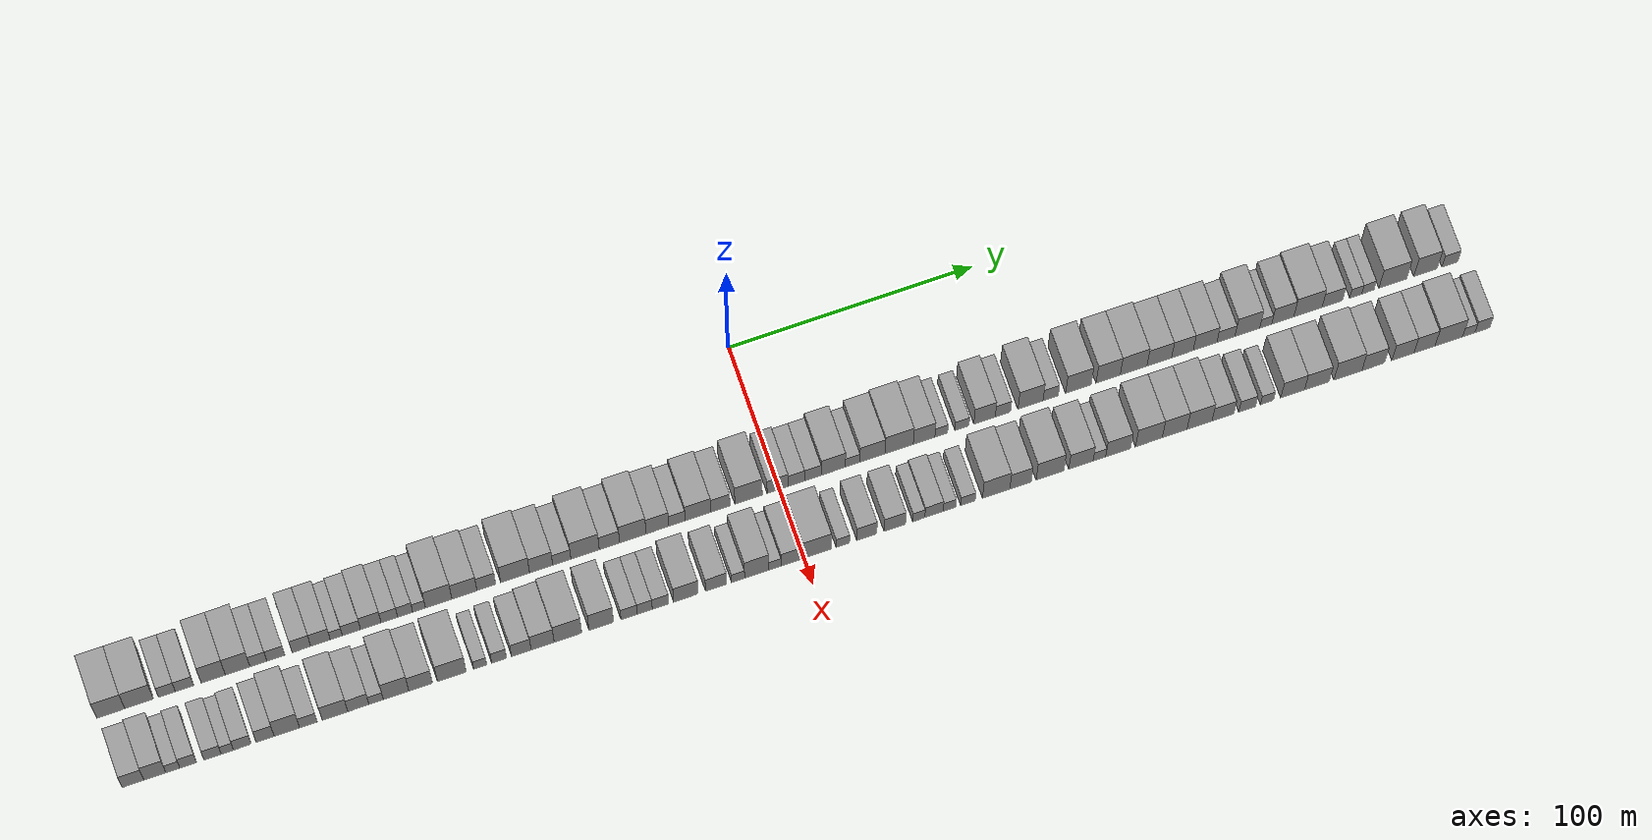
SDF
<sdf version="1.6">
 <world name="default">
  <scene>
   <sky><clouds><speed>12</speed></clouds></sky>
   <ambient>0.4 0.4 0.4 1</ambient>
   <background>0.7 0.7 0.7 1</background>
   <shadows>1</shadows>
  </scene>
  <gravity>0 0 -9.8066</gravity>
  <magnetic_field>6e-06 2.3e-05 -4.2e-05</magnetic_field>
  <physics default="0" name="default_physics" type="ode">
   <ode>
    <solver>
     <type>quick</type>
     <iters>10</iters>
     <sor>1.0</sor>
     <use_dynamic_moi_rescaling>0</use_dynamic_moi_rescaling>
    </solver>
    <constraints>
     <cfm>0</cfm>
     <erp>0.2</erp>
     <contact_max_correcting_vel>100</contact_max_correcting_vel>
     <contact_surface_layer>0.001</contact_surface_layer>
    </constraints>
   </ode>
   <max_step_size>0.004</max_step_size>
   <real_time_factor>1</real_time_factor>
   <real_time_update_rate>250</real_time_update_rate>
  </physics>
  <light name="sun" type="directional">
   <pose>0 0 10 0 0 0</pose>
   <diffuse>0.8 0.8 0.8 1</diffuse>
   <specular>0.2 0.2 0.2 1</specular>
   <attenuation>
    <range>1000</range>
    <constant>0.9</constant>
    <linear>0.01</linear>
    <quadratic>0.001</quadratic>
   </attenuation>
   <direction>-0.5 0.1 -0.9</direction>
  </light>
  <model name="building_1">
   <static>1</static>
   <pose>50.0000 -270.3521 0 0.000000 0.000000 0.000000</pose>
   <link name="link">
    <pose>0 0 12.00 0 0 0</pose>
    <collision name="collision"><geometry><box><size>20.0000 11.2958 24.0000</size></box></geometry></collision>
    <visual name="visual">
     <cast_shadows>0</cast_shadows>
     <geometry><box><size>20.0000 11.2958 24.0000</size></box></geometry>
     <material>
      <script>
       <uri>model://grey_wall/materials/scripts</uri>
       <uri>model://grey_wall/materials/textures</uri>
       <name>vrc/grey_wall</name>
      </script>
     </material>
    </visual>
   </link>
  </model>
  <model name="building_2">
   <static>1</static>
   <pose>50.0000 -258.9503 0 0.000000 0.000000 0.000000</pose>
   <link name="link">
    <pose>0 0 12.00 0 0 0</pose>
    <collision name="collision"><geometry><box><size>20.0000 11.5078 24.0000</size></box></geometry></collision>
    <visual name="visual">
     <cast_shadows>0</cast_shadows>
     <geometry><box><size>20.0000 11.5078 24.0000</size></box></geometry>
     <material>
      <script>
       <uri>model://grey_wall/materials/scripts</uri>
       <uri>model://grey_wall/materials/textures</uri>
       <name>vrc/grey_wall</name>
      </script>
     </material>
    </visual>
   </link>
  </model>
  <model name="building_3">
   <static>1</static>
   <pose>50.0000 -247.7946 0 0.000000 0.000000 0.000000</pose>
   <link name="link">
    <pose>0 0 7.50 0 0 0</pose>
    <collision name="collision"><geometry><box><size>20.0000 6.8036 15.0000</size></box></geometry></collision>
    <visual name="visual">
     <cast_shadows>0</cast_shadows>
     <geometry><box><size>20.0000 6.8036 15.0000</size></box></geometry>
     <material>
      <script>
       <uri>model://grey_wall/materials/scripts</uri>
       <uri>model://grey_wall/materials/textures</uri>
       <name>vrc/grey_wall</name>
      </script>
     </material>
    </visual>
   </link>
  </model>
  <model name="building_4">
   <static>1</static>
   <pose>50.0000 -240.7317 0 0.000000 0.000000 0.000000</pose>
   <link name="link">
    <pose>0 0 7.50 0 0 0</pose>
    <collision name="collision"><geometry><box><size>20.0000 7.3222 15.0000</size></box></geometry></collision>
    <visual name="visual">
     <cast_shadows>0</cast_shadows>
     <geometry><box><size>20.0000 7.3222 15.0000</size></box></geometry>
     <material>
      <script>
       <uri>model://grey_wall/materials/scripts</uri>
       <uri>model://grey_wall/materials/textures</uri>
       <name>vrc/grey_wall</name>
      </script>
     </material>
    </visual>
   </link>
  </model>
  <model name="building_5">
   <static>1</static>
   <pose>50.0000 -229.2101 0 0.000000 0.000000 0.000000</pose>
   <link name="link">
    <pose>0 0 12.00 0 0 0</pose>
    <collision name="collision"><geometry><box><size>20.0000 9.7211 24.0000</size></box></geometry></collision>
    <visual name="visual">
     <cast_shadows>0</cast_shadows>
     <geometry><box><size>20.0000 9.7211 24.0000</size></box></geometry>
     <material>
      <script>
       <uri>model://grey_wall/materials/scripts</uri>
       <uri>model://grey_wall/materials/textures</uri>
       <name>vrc/grey_wall</name>
      </script>
     </material>
    </visual>
   </link>
  </model>
  <model name="building_6">
   <static>1</static>
   <pose>50.0000 -219.4116 0 0.000000 0.000000 0.000000</pose>
   <link name="link">
    <pose>0 0 12.00 0 0 0</pose>
    <collision name="collision"><geometry><box><size>20.0000 9.8758 24.0000</size></box></geometry></collision>
    <visual name="visual">
     <cast_shadows>0</cast_shadows>
     <geometry><box><size>20.0000 9.8758 24.0000</size></box></geometry>
     <material>
      <script>
       <uri>model://grey_wall/materials/scripts</uri>
       <uri>model://grey_wall/materials/textures</uri>
       <name>vrc/grey_wall</name>
      </script>
     </material>
    </visual>
   </link>
  </model>
  <model name="building_7">
   <static>1</static>
   <pose>50.0000 -211.0947 0 0.000000 0.000000 0.000000</pose>
   <link name="link">
    <pose>0 0 7.50 0 0 0</pose>
    <collision name="collision"><geometry><box><size>20.0000 6.7581 15.0000</size></box></geometry></collision>
    <visual name="visual">
     <cast_shadows>0</cast_shadows>
     <geometry><box><size>20.0000 6.7581 15.0000</size></box></geometry>
     <material>
      <script>
       <uri>model://grey_wall/materials/scripts</uri>
       <uri>model://grey_wall/materials/textures</uri>
       <name>vrc/grey_wall</name>
      </script>
     </material>
    </visual>
   </link>
  </model>
  <model name="building_8">
   <static>1</static>
   <pose>50.0000 -204.1174 0 0.000000 0.000000 0.000000</pose>
   <link name="link">
    <pose>0 0 7.50 0 0 0</pose>
    <collision name="collision"><geometry><box><size>20.0000 7.1965 15.0000</size></box></geometry></collision>
    <visual name="visual">
     <cast_shadows>0</cast_shadows>
     <geometry><box><size>20.0000 7.1965 15.0000</size></box></geometry>
     <material>
      <script>
       <uri>model://grey_wall/materials/scripts</uri>
       <uri>model://grey_wall/materials/textures</uri>
       <name>vrc/grey_wall</name>
      </script>
     </material>
    </visual>
   </link>
  </model>
  <model name="building_9">
   <static>1</static>
   <pose>50.0000 -193.7604 0 0.000000 0.000000 0.000000</pose>
   <link name="link">
    <pose>0 0 9.00 0 0 0</pose>
    <collision name="collision"><geometry><box><size>20.0000 7.5175 18.0000</size></box></geometry></collision>
    <visual name="visual">
     <cast_shadows>0</cast_shadows>
     <geometry><box><size>20.0000 7.5175 18.0000</size></box></geometry>
     <material>
      <script>
       <uri>model://grey_wall/materials/scripts</uri>
       <uri>model://grey_wall/materials/textures</uri>
       <name>vrc/grey_wall</name>
      </script>
     </material>
    </visual>
   </link>
  </model>
  <model name="building_10">
   <static>1</static>
   <pose>50.0000 -186.0805 0 0.000000 0.000000 0.000000</pose>
   <link name="link">
    <pose>0 0 9.00 0 0 0</pose>
    <collision name="collision"><geometry><box><size>20.0000 7.8422 18.0000</size></box></geometry></collision>
    <visual name="visual">
     <cast_shadows>0</cast_shadows>
     <geometry><box><size>20.0000 7.8422 18.0000</size></box></geometry>
     <material>
      <script>
       <uri>model://grey_wall/materials/scripts</uri>
       <uri>model://grey_wall/materials/textures</uri>
       <name>vrc/grey_wall</name>
      </script>
     </material>
    </visual>
   </link>
  </model>
  <model name="building_11">
   <static>1</static>
   <pose>50.0000 -179.7081 0 0.000000 0.000000 0.000000</pose>
   <link name="link">
    <pose>0 0 6.00 0 0 0</pose>
    <collision name="collision"><geometry><box><size>20.0000 4.9028 12.0000</size></box></geometry></collision>
    <visual name="visual">
     <cast_shadows>0</cast_shadows>
     <geometry><box><size>20.0000 4.9028 12.0000</size></box></geometry>
     <material>
      <script>
       <uri>model://grey_wall/materials/scripts</uri>
       <uri>model://grey_wall/materials/textures</uri>
       <name>vrc/grey_wall</name>
      </script>
     </material>
    </visual>
   </link>
  </model>
  <model name="building_12">
   <static>1</static>
   <pose>50.0000 -173.6037 0 0.000000 0.000000 0.000000</pose>
   <link name="link">
    <pose>0 0 7.50 0 0 0</pose>
    <collision name="collision"><geometry><box><size>20.0000 7.3061 15.0000</size></box></geometry></collision>
    <visual name="visual">
     <cast_shadows>0</cast_shadows>
     <geometry><box><size>20.0000 7.3061 15.0000</size></box></geometry>
     <material>
      <script>
       <uri>model://grey_wall/materials/scripts</uri>
       <uri>model://grey_wall/materials/textures</uri>
       <name>vrc/grey_wall</name>
      </script>
     </material>
    </visual>
   </link>
  </model>
  <model name="building_13">
   <static>1</static>
   <pose>50.0000 -165.8110 0 0.000000 0.000000 0.000000</pose>
   <link name="link">
    <pose>0 0 9.00 0 0 0</pose>
    <collision name="collision"><geometry><box><size>20.0000 8.2792 18.0000</size></box></geometry></collision>
    <visual name="visual">
     <cast_shadows>0</cast_shadows>
     <geometry><box><size>20.0000 8.2792 18.0000</size></box></geometry>
     <material>
      <script>
       <uri>model://grey_wall/materials/scripts</uri>
       <uri>model://grey_wall/materials/textures</uri>
       <name>vrc/grey_wall</name>
      </script>
     </material>
    </visual>
   </link>
  </model>
  <model name="building_14">
   <static>1</static>
   <pose>50.0000 -158.3307 0 0.000000 0.000000 0.000000</pose>
   <link name="link">
    <pose>0 0 7.50 0 0 0</pose>
    <collision name="collision"><geometry><box><size>20.0000 6.6814 15.0000</size></box></geometry></collision>
    <visual name="visual">
     <cast_shadows>0</cast_shadows>
     <geometry><box><size>20.0000 6.6814 15.0000</size></box></geometry>
     <material>
      <script>
       <uri>model://grey_wall/materials/scripts</uri>
       <uri>model://grey_wall/materials/textures</uri>
       <name>vrc/grey_wall</name>
      </script>
     </material>
    </visual>
   </link>
  </model>
  <model name="building_15">
   <static>1</static>
   <pose>50.0000 -151.9462 0 0.000000 0.000000 0.000000</pose>
   <link name="link">
    <pose>0 0 7.50 0 0 0</pose>
    <collision name="collision"><geometry><box><size>20.0000 6.0876 15.0000</size></box></geometry></collision>
    <visual name="visual">
     <cast_shadows>0</cast_shadows>
     <geometry><box><size>20.0000 6.0876 15.0000</size></box></geometry>
     <material>
      <script>
       <uri>model://grey_wall/materials/scripts</uri>
       <uri>model://grey_wall/materials/textures</uri>
       <name>vrc/grey_wall</name>
      </script>
     </material>
    </visual>
   </link>
  </model>
  <model name="building_16">
   <static>1</static>
   <pose>50.0000 -146.3313 0 0.000000 0.000000 0.000000</pose>
   <link name="link">
    <pose>0 0 6.00 0 0 0</pose>
    <collision name="collision"><geometry><box><size>20.0000 5.1424 12.0000</size></box></geometry></collision>
    <visual name="visual">
     <cast_shadows>0</cast_shadows>
     <geometry><box><size>20.0000 5.1424 12.0000</size></box></geometry>
     <material>
      <script>
       <uri>model://grey_wall/materials/scripts</uri>
       <uri>model://grey_wall/materials/textures</uri>
       <name>vrc/grey_wall</name>
      </script>
     </material>
    </visual>
   </link>
  </model>
  <model name="building_17">
   <static>1</static>
   <pose>50.0000 -138.4068 0 0.000000 0.000000 0.000000</pose>
   <link name="link">
    <pose>0 0 12.00 0 0 0</pose>
    <collision name="collision"><geometry><box><size>20.0000 10.7065 24.0000</size></box></geometry></collision>
    <visual name="visual">
     <cast_shadows>0</cast_shadows>
     <geometry><box><size>20.0000 10.7065 24.0000</size></box></geometry>
     <material>
      <script>
       <uri>model://grey_wall/materials/scripts</uri>
       <uri>model://grey_wall/materials/textures</uri>
       <name>vrc/grey_wall</name>
      </script>
     </material>
    </visual>
   </link>
  </model>
  <model name="building_18">
   <static>1</static>
   <pose>50.0000 -127.9700 0 0.000000 0.000000 0.000000</pose>
   <link name="link">
    <pose>0 0 10.50 0 0 0</pose>
    <collision name="collision"><geometry><box><size>20.0000 10.1671 21.0000</size></box></geometry></collision>
    <visual name="visual">
     <cast_shadows>0</cast_shadows>
     <geometry><box><size>20.0000 10.1671 21.0000</size></box></geometry>
     <material>
      <script>
       <uri>model://grey_wall/materials/scripts</uri>
       <uri>model://grey_wall/materials/textures</uri>
       <name>vrc/grey_wall</name>
      </script>
     </material>
    </visual>
   </link>
  </model>
  <model name="building_19">
   <static>1</static>
   <pose>50.0000 -119.1041 0 0.000000 0.000000 0.000000</pose>
   <link name="link">
    <pose>0 0 9.00 0 0 0</pose>
    <collision name="collision"><geometry><box><size>20.0000 7.5647 18.0000</size></box></geometry></collision>
    <visual name="visual">
     <cast_shadows>0</cast_shadows>
     <geometry><box><size>20.0000 7.5647 18.0000</size></box></geometry>
     <material>
      <script>
       <uri>model://grey_wall/materials/scripts</uri>
       <uri>model://grey_wall/materials/textures</uri>
       <name>vrc/grey_wall</name>
      </script>
     </material>
    </visual>
   </link>
  </model>
  <model name="building_20">
   <static>1</static>
   <pose>50.0000 -107.4591 0 0.000000 0.000000 0.000000</pose>
   <link name="link">
    <pose>0 0 12.00 0 0 0</pose>
    <collision name="collision"><geometry><box><size>20.0000 11.7253 24.0000</size></box></geometry></collision>
    <visual name="visual">
     <cast_shadows>0</cast_shadows>
     <geometry><box><size>20.0000 11.7253 24.0000</size></box></geometry>
     <material>
      <script>
       <uri>model://grey_wall/materials/scripts</uri>
       <uri>model://grey_wall/materials/textures</uri>
       <name>vrc/grey_wall</name>
      </script>
     </material>
    </visual>
   </link>
  </model>
  <model name="building_21">
   <static>1</static>
   <pose>50.0000 -96.9045 0 0.000000 0.000000 0.000000</pose>
   <link name="link">
    <pose>0 0 10.50 0 0 0</pose>
    <collision name="collision"><geometry><box><size>20.0000 9.3840 21.0000</size></box></geometry></collision>
    <visual name="visual">
     <cast_shadows>0</cast_shadows>
     <geometry><box><size>20.0000 9.3840 21.0000</size></box></geometry>
     <material>
      <script>
       <uri>model://grey_wall/materials/scripts</uri>
       <uri>model://grey_wall/materials/textures</uri>
       <name>vrc/grey_wall</name>
      </script>
     </material>
    </visual>
   </link>
  </model>
  <model name="building_22">
   <static>1</static>
   <pose>50.0000 -88.5318 0 0.000000 0.000000 0.000000</pose>
   <link name="link">
    <pose>0 0 7.50 0 0 0</pose>
    <collision name="collision"><geometry><box><size>20.0000 7.3615 15.0000</size></box></geometry></collision>
    <visual name="visual">
     <cast_shadows>0</cast_shadows>
     <geometry><box><size>20.0000 7.3615 15.0000</size></box></geometry>
     <material>
      <script>
       <uri>model://grey_wall/materials/scripts</uri>
       <uri>model://grey_wall/materials/textures</uri>
       <name>vrc/grey_wall</name>
      </script>
     </material>
    </visual>
   </link>
  </model>
  <model name="building_23">
   <static>1</static>
   <pose>50.0000 -79.0962 0 0.000000 0.000000 0.000000</pose>
   <link name="link">
    <pose>0 0 12.00 0 0 0</pose>
    <collision name="collision"><geometry><box><size>20.0000 11.5096 24.0000</size></box></geometry></collision>
    <visual name="visual">
     <cast_shadows>0</cast_shadows>
     <geometry><box><size>20.0000 11.5096 24.0000</size></box></geometry>
     <material>
      <script>
       <uri>model://grey_wall/materials/scripts</uri>
       <uri>model://grey_wall/materials/textures</uri>
       <name>vrc/grey_wall</name>
      </script>
     </material>
    </visual>
   </link>
  </model>
  <model name="building_24">
   <static>1</static>
   <pose>50.0000 -69.2204 0 0.000000 0.000000 0.000000</pose>
   <link name="link">
    <pose>0 0 9.00 0 0 0</pose>
    <collision name="collision"><geometry><box><size>20.0000 8.2421 18.0000</size></box></geometry></collision>
    <visual name="visual">
     <cast_shadows>0</cast_shadows>
     <geometry><box><size>20.0000 8.2421 18.0000</size></box></geometry>
     <material>
      <script>
       <uri>model://grey_wall/materials/scripts</uri>
       <uri>model://grey_wall/materials/textures</uri>
       <name>vrc/grey_wall</name>
      </script>
     </material>
    </visual>
   </link>
  </model>
  <model name="building_25">
   <static>1</static>
   <pose>50.0000 -59.6992 0 0.000000 0.000000 0.000000</pose>
   <link name="link">
    <pose>0 0 12.00 0 0 0</pose>
    <collision name="collision"><geometry><box><size>20.0000 10.8002 24.0000</size></box></geometry></collision>
    <visual name="visual">
     <cast_shadows>0</cast_shadows>
     <geometry><box><size>20.0000 10.8002 24.0000</size></box></geometry>
     <material>
      <script>
       <uri>model://grey_wall/materials/scripts</uri>
       <uri>model://grey_wall/materials/textures</uri>
       <name>vrc/grey_wall</name>
      </script>
     </material>
    </visual>
   </link>
  </model>
  <model name="building_26">
   <static>1</static>
   <pose>50.0000 -49.6911 0 0.000000 0.000000 0.000000</pose>
   <link name="link">
    <pose>0 0 10.50 0 0 0</pose>
    <collision name="collision"><geometry><box><size>20.0000 9.2159 21.0000</size></box></geometry></collision>
    <visual name="visual">
     <cast_shadows>0</cast_shadows>
     <geometry><box><size>20.0000 9.2159 21.0000</size></box></geometry>
     <material>
      <script>
       <uri>model://grey_wall/materials/scripts</uri>
       <uri>model://grey_wall/materials/textures</uri>
       <name>vrc/grey_wall</name>
      </script>
     </material>
    </visual>
   </link>
  </model>
  <model name="building_27">
   <static>1</static>
   <pose>50.0000 -41.7591 0 0.000000 0.000000 0.000000</pose>
   <link name="link">
    <pose>0 0 7.50 0 0 0</pose>
    <collision name="collision"><geometry><box><size>20.0000 6.6481 15.0000</size></box></geometry></collision>
    <visual name="visual">
     <cast_shadows>0</cast_shadows>
     <geometry><box><size>20.0000 6.6481 15.0000</size></box></geometry>
     <material>
      <script>
       <uri>model://grey_wall/materials/scripts</uri>
       <uri>model://grey_wall/materials/textures</uri>
       <name>vrc/grey_wall</name>
      </script>
     </material>
    </visual>
   </link>
  </model>
  <model name="building_28">
   <static>1</static>
   <pose>50.0000 -33.2414 0 0.000000 0.000000 0.000000</pose>
   <link name="link">
    <pose>0 0 10.50 0 0 0</pose>
    <collision name="collision"><geometry><box><size>20.0000 10.3874 21.0000</size></box></geometry></collision>
    <visual name="visual">
     <cast_shadows>0</cast_shadows>
     <geometry><box><size>20.0000 10.3874 21.0000</size></box></geometry>
     <material>
      <script>
       <uri>model://grey_wall/materials/scripts</uri>
       <uri>model://grey_wall/materials/textures</uri>
       <name>vrc/grey_wall</name>
      </script>
     </material>
    </visual>
   </link>
  </model>
  <model name="building_29">
   <static>1</static>
   <pose>50.0000 -24.1255 0 0.000000 0.000000 0.000000</pose>
   <link name="link">
    <pose>0 0 9.00 0 0 0</pose>
    <collision name="collision"><geometry><box><size>20.0000 7.8444 18.0000</size></box></geometry></collision>
    <visual name="visual">
     <cast_shadows>0</cast_shadows>
     <geometry><box><size>20.0000 7.8444 18.0000</size></box></geometry>
     <material>
      <script>
       <uri>model://grey_wall/materials/scripts</uri>
       <uri>model://grey_wall/materials/textures</uri>
       <name>vrc/grey_wall</name>
      </script>
     </material>
    </visual>
   </link>
  </model>
  <model name="building_30">
   <static>1</static>
   <pose>50.0000 -12.6385 0 0.000000 0.000000 0.000000</pose>
   <link name="link">
    <pose>0 0 12.00 0 0 0</pose>
    <collision name="collision"><geometry><box><size>20.0000 11.1297 24.0000</size></box></geometry></collision>
    <visual name="visual">
     <cast_shadows>0</cast_shadows>
     <geometry><box><size>20.0000 11.1297 24.0000</size></box></geometry>
     <material>
      <script>
       <uri>model://grey_wall/materials/scripts</uri>
       <uri>model://grey_wall/materials/textures</uri>
       <name>vrc/grey_wall</name>
      </script>
     </material>
    </visual>
   </link>
  </model>
  <model name="building_31">
   <static>1</static>
   <pose>50.0000 -0.7885 0 0.000000 0.000000 0.000000</pose>
   <link name="link">
    <pose>0 0 9.00 0 0 0</pose>
    <collision name="collision"><geometry><box><size>20.0000 8.5702 18.0000</size></box></geometry></collision>
    <visual name="visual">
     <cast_shadows>0</cast_shadows>
     <geometry><box><size>20.0000 8.5702 18.0000</size></box></geometry>
     <material>
      <script>
       <uri>model://grey_wall/materials/scripts</uri>
       <uri>model://grey_wall/materials/textures</uri>
       <name>vrc/grey_wall</name>
      </script>
     </material>
    </visual>
   </link>
  </model>
  <model name="building_32">
   <static>1</static>
   <pose>50.0000 6.8658 0 0.000000 0.000000 0.000000</pose>
   <link name="link">
    <pose>0 0 7.50 0 0 0</pose>
    <collision name="collision"><geometry><box><size>20.0000 6.7384 15.0000</size></box></geometry></collision>
    <visual name="visual">
     <cast_shadows>0</cast_shadows>
     <geometry><box><size>20.0000 6.7384 15.0000</size></box></geometry>
     <material>
      <script>
       <uri>model://grey_wall/materials/scripts</uri>
       <uri>model://grey_wall/materials/textures</uri>
       <name>vrc/grey_wall</name>
      </script>
     </material>
    </visual>
   </link>
  </model>
  <model name="building_33">
   <static>1</static>
   <pose>50.0000 13.6078 0 0.000000 0.000000 0.000000</pose>
   <link name="link">
    <pose>0 0 7.50 0 0 0</pose>
    <collision name="collision"><geometry><box><size>20.0000 6.7456 15.0000</size></box></geometry></collision>
    <visual name="visual">
     <cast_shadows>0</cast_shadows>
     <geometry><box><size>20.0000 6.7456 15.0000</size></box></geometry>
     <material>
      <script>
       <uri>model://grey_wall/materials/scripts</uri>
       <uri>model://grey_wall/materials/textures</uri>
       <name>vrc/grey_wall</name>
      </script>
     </material>
    </visual>
   </link>
  </model>
  <model name="building_34">
   <static>1</static>
   <pose>50.0000 21.9241 0 0.000000 0.000000 0.000000</pose>
   <link name="link">
    <pose>0 0 10.50 0 0 0</pose>
    <collision name="collision"><geometry><box><size>20.0000 9.8871 21.0000</size></box></geometry></collision>
    <visual name="visual">
     <cast_shadows>0</cast_shadows>
     <geometry><box><size>20.0000 9.8871 21.0000</size></box></geometry>
     <material>
      <script>
       <uri>model://grey_wall/materials/scripts</uri>
       <uri>model://grey_wall/materials/textures</uri>
       <name>vrc/grey_wall</name>
      </script>
     </material>
    </visual>
   </link>
  </model>
  <model name="building_35">
   <static>1</static>
   <pose>50.0000 29.8331 0 0.000000 0.000000 0.000000</pose>
   <link name="link">
    <pose>0 0 6.00 0 0 0</pose>
    <collision name="collision"><geometry><box><size>20.0000 5.9308 12.0000</size></box></geometry></collision>
    <visual name="visual">
     <cast_shadows>0</cast_shadows>
     <geometry><box><size>20.0000 5.9308 12.0000</size></box></geometry>
     <material>
      <script>
       <uri>model://grey_wall/materials/scripts</uri>
       <uri>model://grey_wall/materials/textures</uri>
       <name>vrc/grey_wall</name>
      </script>
     </material>
    </visual>
   </link>
  </model>
  <model name="building_36">
   <static>1</static>
   <pose>50.0000 37.9600 0 0.000000 0.000000 0.000000</pose>
   <link name="link">
    <pose>0 0 10.50 0 0 0</pose>
    <collision name="collision"><geometry><box><size>20.0000 10.3231 21.0000</size></box></geometry></collision>
    <visual name="visual">
     <cast_shadows>0</cast_shadows>
     <geometry><box><size>20.0000 10.3231 21.0000</size></box></geometry>
     <material>
      <script>
       <uri>model://grey_wall/materials/scripts</uri>
       <uri>model://grey_wall/materials/textures</uri>
       <name>vrc/grey_wall</name>
      </script>
     </material>
    </visual>
   </link>
  </model>
  <model name="building_37">
   <static>1</static>
   <pose>50.0000 48.8931 0 0.000000 0.000000 0.000000</pose>
   <link name="link">
    <pose>0 0 12.00 0 0 0</pose>
    <collision name="collision"><geometry><box><size>20.0000 11.5431 24.0000</size></box></geometry></collision>
    <visual name="visual">
     <cast_shadows>0</cast_shadows>
     <geometry><box><size>20.0000 11.5431 24.0000</size></box></geometry>
     <material>
      <script>
       <uri>model://grey_wall/materials/scripts</uri>
       <uri>model://grey_wall/materials/textures</uri>
       <name>vrc/grey_wall</name>
      </script>
     </material>
    </visual>
   </link>
  </model>
  <model name="building_38">
   <static>1</static>
   <pose>50.0000 59.0876 0 0.000000 0.000000 0.000000</pose>
   <link name="link">
    <pose>0 0 10.50 0 0 0</pose>
    <collision name="collision"><geometry><box><size>20.0000 8.8458 21.0000</size></box></geometry></collision>
    <visual name="visual">
     <cast_shadows>0</cast_shadows>
     <geometry><box><size>20.0000 8.8458 21.0000</size></box></geometry>
     <material>
      <script>
       <uri>model://grey_wall/materials/scripts</uri>
       <uri>model://grey_wall/materials/textures</uri>
       <name>vrc/grey_wall</name>
      </script>
     </material>
    </visual>
   </link>
  </model>
  <model name="building_39">
   <static>1</static>
   <pose>50.0000 66.1097 0 0.000000 0.000000 0.000000</pose>
   <link name="link">
    <pose>0 0 6.00 0 0 0</pose>
    <collision name="collision"><geometry><box><size>20.0000 5.1983 12.0000</size></box></geometry></collision>
    <visual name="visual">
     <cast_shadows>0</cast_shadows>
     <geometry><box><size>20.0000 5.1983 12.0000</size></box></geometry>
     <material>
      <script>
       <uri>model://grey_wall/materials/scripts</uri>
       <uri>model://grey_wall/materials/textures</uri>
       <name>vrc/grey_wall</name>
      </script>
     </material>
    </visual>
   </link>
  </model>
  <model name="building_40">
   <static>1</static>
   <pose>50.0000 74.5952 0 0.000000 0.000000 0.000000</pose>
   <link name="link">
    <pose>0 0 6.00 0 0 0</pose>
    <collision name="collision"><geometry><box><size>20.0000 5.7728 12.0000</size></box></geometry></collision>
    <visual name="visual">
     <cast_shadows>0</cast_shadows>
     <geometry><box><size>20.0000 5.7728 12.0000</size></box></geometry>
     <material>
      <script>
       <uri>model://grey_wall/materials/scripts</uri>
       <uri>model://grey_wall/materials/textures</uri>
       <name>vrc/grey_wall</name>
      </script>
     </material>
    </visual>
   </link>
  </model>
  <model name="building_41">
   <static>1</static>
   <pose>50.0000 83.8726 0 0.000000 0.000000 0.000000</pose>
   <link name="link">
    <pose>0 0 10.50 0 0 0</pose>
    <collision name="collision"><geometry><box><size>20.0000 8.7820 21.0000</size></box></geometry></collision>
    <visual name="visual">
     <cast_shadows>0</cast_shadows>
     <geometry><box><size>20.0000 8.7820 21.0000</size></box></geometry>
     <material>
      <script>
       <uri>model://grey_wall/materials/scripts</uri>
       <uri>model://grey_wall/materials/textures</uri>
       <name>vrc/grey_wall</name>
      </script>
     </material>
    </visual>
   </link>
  </model>
  <model name="building_42">
   <static>1</static>
   <pose>50.0000 91.4099 0 0.000000 0.000000 0.000000</pose>
   <link name="link">
    <pose>0 0 7.50 0 0 0</pose>
    <collision name="collision"><geometry><box><size>20.0000 6.2925 15.0000</size></box></geometry></collision>
    <visual name="visual">
     <cast_shadows>0</cast_shadows>
     <geometry><box><size>20.0000 6.2925 15.0000</size></box></geometry>
     <material>
      <script>
       <uri>model://grey_wall/materials/scripts</uri>
       <uri>model://grey_wall/materials/textures</uri>
       <name>vrc/grey_wall</name>
      </script>
     </material>
    </visual>
   </link>
  </model>
  <model name="building_43">
   <static>1</static>
   <pose>50.0000 102.6996 0 0.000000 0.000000 0.000000</pose>
   <link name="link">
    <pose>0 0 12.00 0 0 0</pose>
    <collision name="collision"><geometry><box><size>20.0000 10.2869 24.0000</size></box></geometry></collision>
    <visual name="visual">
     <cast_shadows>0</cast_shadows>
     <geometry><box><size>20.0000 10.2869 24.0000</size></box></geometry>
     <material>
      <script>
       <uri>model://grey_wall/materials/scripts</uri>
       <uri>model://grey_wall/materials/textures</uri>
       <name>vrc/grey_wall</name>
      </script>
     </material>
    </visual>
   </link>
  </model>
  <model name="building_44">
   <static>1</static>
   <pose>50.0000 110.9824 0 0.000000 0.000000 0.000000</pose>
   <link name="link">
    <pose>0 0 7.50 0 0 0</pose>
    <collision name="collision"><geometry><box><size>20.0000 6.2788 15.0000</size></box></geometry></collision>
    <visual name="visual">
     <cast_shadows>0</cast_shadows>
     <geometry><box><size>20.0000 6.2788 15.0000</size></box></geometry>
     <material>
      <script>
       <uri>model://grey_wall/materials/scripts</uri>
       <uri>model://grey_wall/materials/textures</uri>
       <name>vrc/grey_wall</name>
      </script>
     </material>
    </visual>
   </link>
  </model>
  <model name="building_45">
   <static>1</static>
   <pose>50.0000 122.3922 0 0.000000 0.000000 0.000000</pose>
   <link name="link">
    <pose>0 0 12.00 0 0 0</pose>
    <collision name="collision"><geometry><box><size>20.0000 10.5407 24.0000</size></box></geometry></collision>
    <visual name="visual">
     <cast_shadows>0</cast_shadows>
     <geometry><box><size>20.0000 10.5407 24.0000</size></box></geometry>
     <material>
      <script>
       <uri>model://grey_wall/materials/scripts</uri>
       <uri>model://grey_wall/materials/textures</uri>
       <name>vrc/grey_wall</name>
      </script>
     </material>
    </visual>
   </link>
  </model>
  <model name="building_46">
   <static>1</static>
   <pose>50.0000 134.6356 0 0.000000 0.000000 0.000000</pose>
   <link name="link">
    <pose>0 0 12.00 0 0 0</pose>
    <collision name="collision"><geometry><box><size>20.0000 9.9462 24.0000</size></box></geometry></collision>
    <visual name="visual">
     <cast_shadows>0</cast_shadows>
     <geometry><box><size>20.0000 9.9462 24.0000</size></box></geometry>
     <material>
      <script>
       <uri>model://grey_wall/materials/scripts</uri>
       <uri>model://grey_wall/materials/textures</uri>
       <name>vrc/grey_wall</name>
      </script>
     </material>
    </visual>
   </link>
  </model>
  <model name="building_47">
   <static>1</static>
   <pose>50.0000 145.1121 0 0.000000 0.000000 0.000000</pose>
   <link name="link">
    <pose>0 0 12.00 0 0 0</pose>
    <collision name="collision"><geometry><box><size>20.0000 11.0066 24.0000</size></box></geometry></collision>
    <visual name="visual">
     <cast_shadows>0</cast_shadows>
     <geometry><box><size>20.0000 11.0066 24.0000</size></box></geometry>
     <material>
      <script>
       <uri>model://grey_wall/materials/scripts</uri>
       <uri>model://grey_wall/materials/textures</uri>
       <name>vrc/grey_wall</name>
      </script>
     </material>
    </visual>
   </link>
  </model>
  <model name="building_48">
   <static>1</static>
   <pose>50.0000 155.7052 0 0.000000 0.000000 0.000000</pose>
   <link name="link">
    <pose>0 0 10.50 0 0 0</pose>
    <collision name="collision"><geometry><box><size>20.0000 10.1797 21.0000</size></box></geometry></collision>
    <visual name="visual">
     <cast_shadows>0</cast_shadows>
     <geometry><box><size>20.0000 10.1797 21.0000</size></box></geometry>
     <material>
      <script>
       <uri>model://grey_wall/materials/scripts</uri>
       <uri>model://grey_wall/materials/textures</uri>
       <name>vrc/grey_wall</name>
      </script>
     </material>
    </visual>
   </link>
  </model>
  <model name="building_49">
   <static>1</static>
   <pose>50.0000 165.2450 0 0.000000 0.000000 0.000000</pose>
   <link name="link">
    <pose>0 0 10.50 0 0 0</pose>
    <collision name="collision"><geometry><box><size>20.0000 8.8998 21.0000</size></box></geometry></collision>
    <visual name="visual">
     <cast_shadows>0</cast_shadows>
     <geometry><box><size>20.0000 8.8998 21.0000</size></box></geometry>
     <material>
      <script>
       <uri>model://grey_wall/materials/scripts</uri>
       <uri>model://grey_wall/materials/textures</uri>
       <name>vrc/grey_wall</name>
      </script>
     </material>
    </visual>
   </link>
  </model>
  <model name="building_50">
   <static>1</static>
   <pose>50.0000 174.5735 0 0.000000 0.000000 0.000000</pose>
   <link name="link">
    <pose>0 0 10.50 0 0 0</pose>
    <collision name="collision"><geometry><box><size>20.0000 9.7571 21.0000</size></box></geometry></collision>
    <visual name="visual">
     <cast_shadows>0</cast_shadows>
     <geometry><box><size>20.0000 9.7571 21.0000</size></box></geometry>
     <material>
      <script>
       <uri>model://grey_wall/materials/scripts</uri>
       <uri>model://grey_wall/materials/textures</uri>
       <name>vrc/grey_wall</name>
      </script>
     </material>
    </visual>
   </link>
  </model>
  <model name="building_51">
   <static>1</static>
   <pose>50.0000 183.1616 0 0.000000 0.000000 0.000000</pose>
   <link name="link">
    <pose>0 0 7.50 0 0 0</pose>
    <collision name="collision"><geometry><box><size>20.0000 7.4192 15.0000</size></box></geometry></collision>
    <visual name="visual">
     <cast_shadows>0</cast_shadows>
     <geometry><box><size>20.0000 7.4192 15.0000</size></box></geometry>
     <material>
      <script>
       <uri>model://grey_wall/materials/scripts</uri>
       <uri>model://grey_wall/materials/textures</uri>
       <name>vrc/grey_wall</name>
      </script>
     </material>
    </visual>
   </link>
  </model>
  <model name="building_52">
   <static>1</static>
   <pose>50.0000 192.0234 0 0.000000 0.000000 0.000000</pose>
   <link name="link">
    <pose>0 0 12.00 0 0 0</pose>
    <collision name="collision"><geometry><box><size>20.0000 10.3044 24.0000</size></box></geometry></collision>
    <visual name="visual">
     <cast_shadows>0</cast_shadows>
     <geometry><box><size>20.0000 10.3044 24.0000</size></box></geometry>
     <material>
      <script>
       <uri>model://grey_wall/materials/scripts</uri>
       <uri>model://grey_wall/materials/textures</uri>
       <name>vrc/grey_wall</name>
      </script>
     </material>
    </visual>
   </link>
  </model>
  <model name="building_53">
   <static>1</static>
   <pose>50.0000 199.6400 0 0.000000 0.000000 0.000000</pose>
   <link name="link">
    <pose>0 0 6.00 0 0 0</pose>
    <collision name="collision"><geometry><box><size>20.0000 4.9287 12.0000</size></box></geometry></collision>
    <visual name="visual">
     <cast_shadows>0</cast_shadows>
     <geometry><box><size>20.0000 4.9287 12.0000</size></box></geometry>
     <material>
      <script>
       <uri>model://grey_wall/materials/scripts</uri>
       <uri>model://grey_wall/materials/textures</uri>
       <name>vrc/grey_wall</name>
      </script>
     </material>
    </visual>
   </link>
  </model>
  <model name="building_54">
   <static>1</static>
   <pose>50.0000 206.6869 0 0.000000 0.000000 0.000000</pose>
   <link name="link">
    <pose>0 0 10.50 0 0 0</pose>
    <collision name="collision"><geometry><box><size>20.0000 9.1651 21.0000</size></box></geometry></collision>
    <visual name="visual">
     <cast_shadows>0</cast_shadows>
     <geometry><box><size>20.0000 9.1651 21.0000</size></box></geometry>
     <material>
      <script>
       <uri>model://grey_wall/materials/scripts</uri>
       <uri>model://grey_wall/materials/textures</uri>
       <name>vrc/grey_wall</name>
      </script>
     </material>
    </visual>
   </link>
  </model>
  <model name="building_55">
   <static>1</static>
   <pose>50.0000 217.1138 0 0.000000 0.000000 0.000000</pose>
   <link name="link">
    <pose>0 0 12.00 0 0 0</pose>
    <collision name="collision"><geometry><box><size>20.0000 11.6887 24.0000</size></box></geometry></collision>
    <visual name="visual">
     <cast_shadows>0</cast_shadows>
     <geometry><box><size>20.0000 11.6887 24.0000</size></box></geometry>
     <material>
      <script>
       <uri>model://grey_wall/materials/scripts</uri>
       <uri>model://grey_wall/materials/textures</uri>
       <name>vrc/grey_wall</name>
      </script>
     </material>
    </visual>
   </link>
  </model>
  <model name="building_56">
   <static>1</static>
   <pose>50.0000 227.1906 0 0.000000 0.000000 0.000000</pose>
   <link name="link">
    <pose>0 0 9.00 0 0 0</pose>
    <collision name="collision"><geometry><box><size>20.0000 8.4649 18.0000</size></box></geometry></collision>
    <visual name="visual">
     <cast_shadows>0</cast_shadows>
     <geometry><box><size>20.0000 8.4649 18.0000</size></box></geometry>
     <material>
      <script>
       <uri>model://grey_wall/materials/scripts</uri>
       <uri>model://grey_wall/materials/textures</uri>
       <name>vrc/grey_wall</name>
      </script>
     </material>
    </visual>
   </link>
  </model>
  <model name="building_57">
   <static>1</static>
   <pose>50.0000 236.9264 0 0.000000 0.000000 0.000000</pose>
   <link name="link">
    <pose>0 0 6.00 0 0 0</pose>
    <collision name="collision"><geometry><box><size>20.0000 5.0067 12.0000</size></box></geometry></collision>
    <visual name="visual">
     <cast_shadows>0</cast_shadows>
     <geometry><box><size>20.0000 5.0067 12.0000</size></box></geometry>
     <material>
      <script>
       <uri>model://grey_wall/materials/scripts</uri>
       <uri>model://grey_wall/materials/textures</uri>
       <name>vrc/grey_wall</name>
      </script>
     </material>
    </visual>
   </link>
  </model>
  <model name="building_58">
   <static>1</static>
   <pose>50.0000 241.9658 0 0.000000 0.000000 0.000000</pose>
   <link name="link">
    <pose>0 0 6.00 0 0 0</pose>
    <collision name="collision"><geometry><box><size>20.0000 5.0721 12.0000</size></box></geometry></collision>
    <visual name="visual">
     <cast_shadows>0</cast_shadows>
     <geometry><box><size>20.0000 5.0721 12.0000</size></box></geometry>
     <material>
      <script>
       <uri>model://grey_wall/materials/scripts</uri>
       <uri>model://grey_wall/materials/textures</uri>
       <name>vrc/grey_wall</name>
      </script>
     </material>
    </visual>
   </link>
  </model>
  <model name="building_59">
   <static>1</static>
   <pose>50.0000 252.2399 0 0.000000 0.000000 0.000000</pose>
   <link name="link">
    <pose>0 0 12.00 0 0 0</pose>
    <collision name="collision"><geometry><box><size>20.0000 11.4761 24.0000</size></box></geometry></collision>
    <visual name="visual">
     <cast_shadows>0</cast_shadows>
     <geometry><box><size>20.0000 11.4761 24.0000</size></box></geometry>
     <material>
      <script>
       <uri>model://grey_wall/materials/scripts</uri>
       <uri>model://grey_wall/materials/textures</uri>
       <name>vrc/grey_wall</name>
      </script>
     </material>
    </visual>
   </link>
  </model>
  <model name="building_60">
   <static>1</static>
   <pose>50.0000 265.8508 0 0.000000 0.000000 0.000000</pose>
   <link name="link">
    <pose>0 0 12.00 0 0 0</pose>
    <collision name="collision"><geometry><box><size>20.0000 9.7458 24.0000</size></box></geometry></collision>
    <visual name="visual">
     <cast_shadows>0</cast_shadows>
     <geometry><box><size>20.0000 9.7458 24.0000</size></box></geometry>
     <material>
      <script>
       <uri>model://grey_wall/materials/scripts</uri>
       <uri>model://grey_wall/materials/textures</uri>
       <name>vrc/grey_wall</name>
      </script>
     </material>
    </visual>
   </link>
  </model>
  <model name="building_61">
   <static>1</static>
   <pose>50.0000 275.9889 0 0.000000 0.000000 0.000000</pose>
   <link name="link">
    <pose>0 0 7.50 0 0 0</pose>
    <collision name="collision"><geometry><box><size>20.0000 6.5304 15.0000</size></box></geometry></collision>
    <visual name="visual">
     <cast_shadows>0</cast_shadows>
     <geometry><box><size>20.0000 6.5304 15.0000</size></box></geometry>
     <material>
      <script>
       <uri>model://grey_wall/materials/scripts</uri>
       <uri>model://grey_wall/materials/textures</uri>
       <name>vrc/grey_wall</name>
      </script>
     </material>
    </visual>
   </link>
  </model>
  <model name="building_62">
   <static>1</static>
   <pose>79.0000 -270.6561 0 0.000000 0.000000 0.000000</pose>
   <link name="link">
    <pose>0 0 9.00 0 0 0</pose>
    <collision name="collision"><geometry><box><size>20.0000 8.6878 18.0000</size></box></geometry></collision>
    <visual name="visual">
     <cast_shadows>0</cast_shadows>
     <geometry><box><size>20.0000 8.6878 18.0000</size></box></geometry>
     <material>
      <script>
       <uri>model://grey_wall/materials/scripts</uri>
       <uri>model://grey_wall/materials/textures</uri>
       <name>vrc/grey_wall</name>
      </script>
     </material>
    </visual>
   </link>
  </model>
  <model name="building_63">
   <static>1</static>
   <pose>79.0000 -261.8974 0 0.000000 0.000000 0.000000</pose>
   <link name="link">
    <pose>0 0 10.50 0 0 0</pose>
    <collision name="collision"><geometry><box><size>20.0000 8.8296 21.0000</size></box></geometry></collision>
    <visual name="visual">
     <cast_shadows>0</cast_shadows>
     <geometry><box><size>20.0000 8.8296 21.0000</size></box></geometry>
     <material>
      <script>
       <uri>model://grey_wall/materials/scripts</uri>
       <uri>model://grey_wall/materials/textures</uri>
       <name>vrc/grey_wall</name>
      </script>
     </material>
    </visual>
   </link>
  </model>
  <model name="building_64">
   <static>1</static>
   <pose>79.0000 -254.6926 0 0.000000 0.000000 0.000000</pose>
   <link name="link">
    <pose>0 0 6.00 0 0 0</pose>
    <collision name="collision"><geometry><box><size>20.0000 5.5800 12.0000</size></box></geometry></collision>
    <visual name="visual">
     <cast_shadows>0</cast_shadows>
     <geometry><box><size>20.0000 5.5800 12.0000</size></box></geometry>
     <material>
      <script>
       <uri>model://grey_wall/materials/scripts</uri>
       <uri>model://grey_wall/materials/textures</uri>
       <name>vrc/grey_wall</name>
      </script>
     </material>
    </visual>
   </link>
  </model>
  <model name="building_65">
   <static>1</static>
   <pose>79.0000 -248.5726 0 0.000000 0.000000 0.000000</pose>
   <link name="link">
    <pose>0 0 7.50 0 0 0</pose>
    <collision name="collision"><geometry><box><size>20.0000 6.6600 15.0000</size></box></geometry></collision>
    <visual name="visual">
     <cast_shadows>0</cast_shadows>
     <geometry><box><size>20.0000 6.6600 15.0000</size></box></geometry>
     <material>
      <script>
       <uri>model://grey_wall/materials/scripts</uri>
       <uri>model://grey_wall/materials/textures</uri>
       <name>vrc/grey_wall</name>
      </script>
     </material>
    </visual>
   </link>
  </model>
  <model name="building_66">
   <static>1</static>
   <pose>79.0000 -238.7857 0 0.000000 0.000000 0.000000</pose>
   <link name="link">
    <pose>0 0 7.50 0 0 0</pose>
    <collision name="collision"><geometry><box><size>20.0000 6.9138 15.0000</size></box></geometry></collision>
    <visual name="visual">
     <cast_shadows>0</cast_shadows>
     <geometry><box><size>20.0000 6.9138 15.0000</size></box></geometry>
     <material>
      <script>
       <uri>model://grey_wall/materials/scripts</uri>
       <uri>model://grey_wall/materials/textures</uri>
       <name>vrc/grey_wall</name>
      </script>
     </material>
    </visual>
   </link>
  </model>
  <model name="building_67">
   <static>1</static>
   <pose>79.0000 -232.8735 0 0.000000 0.000000 0.000000</pose>
   <link name="link">
    <pose>0 0 6.00 0 0 0</pose>
    <collision name="collision"><geometry><box><size>20.0000 4.9106 12.0000</size></box></geometry></collision>
    <visual name="visual">
     <cast_shadows>0</cast_shadows>
     <geometry><box><size>20.0000 4.9106 12.0000</size></box></geometry>
     <material>
      <script>
       <uri>model://grey_wall/materials/scripts</uri>
       <uri>model://grey_wall/materials/textures</uri>
       <name>vrc/grey_wall</name>
      </script>
     </material>
    </visual>
   </link>
  </model>
  <model name="building_68">
   <static>1</static>
   <pose>79.0000 -226.8763 0 0.000000 0.000000 0.000000</pose>
   <link name="link">
    <pose>0 0 7.50 0 0 0</pose>
    <collision name="collision"><geometry><box><size>20.0000 7.0837 15.0000</size></box></geometry></collision>
    <visual name="visual">
     <cast_shadows>0</cast_shadows>
     <geometry><box><size>20.0000 7.0837 15.0000</size></box></geometry>
     <material>
      <script>
       <uri>model://grey_wall/materials/scripts</uri>
       <uri>model://grey_wall/materials/textures</uri>
       <name>vrc/grey_wall</name>
      </script>
     </material>
    </visual>
   </link>
  </model>
  <model name="building_69">
   <static>1</static>
   <pose>79.0000 -217.7282 0 0.000000 0.000000 0.000000</pose>
   <link name="link">
    <pose>0 0 9.00 0 0 0</pose>
    <collision name="collision"><geometry><box><size>20.0000 7.2126 18.0000</size></box></geometry></collision>
    <visual name="visual">
     <cast_shadows>0</cast_shadows>
     <geometry><box><size>20.0000 7.2126 18.0000</size></box></geometry>
     <material>
      <script>
       <uri>model://grey_wall/materials/scripts</uri>
       <uri>model://grey_wall/materials/textures</uri>
       <name>vrc/grey_wall</name>
      </script>
     </material>
    </visual>
   </link>
  </model>
  <model name="building_70">
   <static>1</static>
   <pose>79.0000 -209.0349 0 0.000000 0.000000 0.000000</pose>
   <link name="link">
    <pose>0 0 12.00 0 0 0</pose>
    <collision name="collision"><geometry><box><size>20.0000 10.1741 24.0000</size></box></geometry></collision>
    <visual name="visual">
     <cast_shadows>0</cast_shadows>
     <geometry><box><size>20.0000 10.1741 24.0000</size></box></geometry>
     <material>
      <script>
       <uri>model://grey_wall/materials/scripts</uri>
       <uri>model://grey_wall/materials/textures</uri>
       <name>vrc/grey_wall</name>
      </script>
     </material>
    </visual>
   </link>
  </model>
  <model name="building_71">
   <static>1</static>
   <pose>79.0000 -200.4182 0 0.000000 0.000000 0.000000</pose>
   <link name="link">
    <pose>0 0 7.50 0 0 0</pose>
    <collision name="collision"><geometry><box><size>20.0000 7.0592 15.0000</size></box></geometry></collision>
    <visual name="visual">
     <cast_shadows>0</cast_shadows>
     <geometry><box><size>20.0000 7.0592 15.0000</size></box></geometry>
     <material>
      <script>
       <uri>model://grey_wall/materials/scripts</uri>
       <uri>model://grey_wall/materials/textures</uri>
       <name>vrc/grey_wall</name>
      </script>
     </material>
    </visual>
   </link>
  </model>
  <model name="building_72">
   <static>1</static>
   <pose>79.0000 -189.7333 0 0.000000 0.000000 0.000000</pose>
   <link name="link">
    <pose>0 0 10.50 0 0 0</pose>
    <collision name="collision"><geometry><box><size>20.0000 10.3107 21.0000</size></box></geometry></collision>
    <visual name="visual">
     <cast_shadows>0</cast_shadows>
     <geometry><box><size>20.0000 10.3107 21.0000</size></box></geometry>
     <material>
      <script>
       <uri>model://grey_wall/materials/scripts</uri>
       <uri>model://grey_wall/materials/textures</uri>
       <name>vrc/grey_wall</name>
      </script>
     </material>
    </visual>
   </link>
  </model>
  <model name="building_73">
   <static>1</static>
   <pose>79.0000 -180.3293 0 0.000000 0.000000 0.000000</pose>
   <link name="link">
    <pose>0 0 9.00 0 0 0</pose>
    <collision name="collision"><geometry><box><size>20.0000 8.4972 18.0000</size></box></geometry></collision>
    <visual name="visual">
     <cast_shadows>0</cast_shadows>
     <geometry><box><size>20.0000 8.4972 18.0000</size></box></geometry>
     <material>
      <script>
       <uri>model://grey_wall/materials/scripts</uri>
       <uri>model://grey_wall/materials/textures</uri>
       <name>vrc/grey_wall</name>
      </script>
     </material>
    </visual>
   </link>
  </model>
  <model name="building_74">
   <static>1</static>
   <pose>79.0000 -173.1874 0 0.000000 0.000000 0.000000</pose>
   <link name="link">
    <pose>0 0 6.00 0 0 0</pose>
    <collision name="collision"><geometry><box><size>20.0000 5.7867 12.0000</size></box></geometry></collision>
    <visual name="visual">
     <cast_shadows>0</cast_shadows>
     <geometry><box><size>20.0000 5.7867 12.0000</size></box></geometry>
     <material>
      <script>
       <uri>model://grey_wall/materials/scripts</uri>
       <uri>model://grey_wall/materials/textures</uri>
       <name>vrc/grey_wall</name>
      </script>
     </material>
    </visual>
   </link>
  </model>
  <model name="building_75">
   <static>1</static>
   <pose>79.0000 -165.1717 0 0.000000 0.000000 0.000000</pose>
   <link name="link">
    <pose>0 0 12.00 0 0 0</pose>
    <collision name="collision"><geometry><box><size>20.0000 10.2445 24.0000</size></box></geometry></collision>
    <visual name="visual">
     <cast_shadows>0</cast_shadows>
     <geometry><box><size>20.0000 10.2445 24.0000</size></box></geometry>
     <material>
      <script>
       <uri>model://grey_wall/materials/scripts</uri>
       <uri>model://grey_wall/materials/textures</uri>
       <name>vrc/grey_wall</name>
      </script>
     </material>
    </visual>
   </link>
  </model>
  <model name="building_76">
   <static>1</static>
   <pose>79.0000 -155.2880 0 0.000000 0.000000 0.000000</pose>
   <link name="link">
    <pose>0 0 10.50 0 0 0</pose>
    <collision name="collision"><geometry><box><size>20.0000 9.5230 21.0000</size></box></geometry></collision>
    <visual name="visual">
     <cast_shadows>0</cast_shadows>
     <geometry><box><size>20.0000 9.5230 21.0000</size></box></geometry>
     <material>
      <script>
       <uri>model://grey_wall/materials/scripts</uri>
       <uri>model://grey_wall/materials/textures</uri>
       <name>vrc/grey_wall</name>
      </script>
     </material>
    </visual>
   </link>
  </model>
  <model name="building_77">
   <static>1</static>
   <pose>79.0000 -142.7091 0 0.000000 0.000000 0.000000</pose>
   <link name="link">
    <pose>0 0 12.00 0 0 0</pose>
    <collision name="collision"><geometry><box><size>20.0000 11.6348 24.0000</size></box></geometry></collision>
    <visual name="visual">
     <cast_shadows>0</cast_shadows>
     <geometry><box><size>20.0000 11.6348 24.0000</size></box></geometry>
     <material>
      <script>
       <uri>model://grey_wall/materials/scripts</uri>
       <uri>model://grey_wall/materials/textures</uri>
       <name>vrc/grey_wall</name>
      </script>
     </material>
    </visual>
   </link>
  </model>
  <model name="building_78">
   <static>1</static>
   <pose>79.0000 -131.2579 0 0.000000 0.000000 0.000000</pose>
   <link name="link">
    <pose>0 0 6.00 0 0 0</pose>
    <collision name="collision"><geometry><box><size>20.0000 5.2676 12.0000</size></box></geometry></collision>
    <visual name="visual">
     <cast_shadows>0</cast_shadows>
     <geometry><box><size>20.0000 5.2676 12.0000</size></box></geometry>
     <material>
      <script>
       <uri>model://grey_wall/materials/scripts</uri>
       <uri>model://grey_wall/materials/textures</uri>
       <name>vrc/grey_wall</name>
      </script>
     </material>
    </visual>
   </link>
  </model>
  <model name="building_79">
   <static>1</static>
   <pose>79.0000 -123.6107 0 0.000000 0.000000 0.000000</pose>
   <link name="link">
    <pose>0 0 7.50 0 0 0</pose>
    <collision name="collision"><geometry><box><size>20.0000 6.0268 15.0000</size></box></geometry></collision>
    <visual name="visual">
     <cast_shadows>0</cast_shadows>
     <geometry><box><size>20.0000 6.0268 15.0000</size></box></geometry>
     <material>
      <script>
       <uri>model://grey_wall/materials/scripts</uri>
       <uri>model://grey_wall/materials/textures</uri>
       <name>vrc/grey_wall</name>
      </script>
     </material>
    </visual>
   </link>
  </model>
  <model name="building_80">
   <static>1</static>
   <pose>79.0000 -114.6585 0 0.000000 0.000000 0.000000</pose>
   <link name="link">
    <pose>0 0 9.00 0 0 0</pose>
    <collision name="collision"><geometry><box><size>20.0000 7.8775 18.0000</size></box></geometry></collision>
    <visual name="visual">
     <cast_shadows>0</cast_shadows>
     <geometry><box><size>20.0000 7.8775 18.0000</size></box></geometry>
     <material>
      <script>
       <uri>model://grey_wall/materials/scripts</uri>
       <uri>model://grey_wall/materials/textures</uri>
       <name>vrc/grey_wall</name>
      </script>
     </material>
    </visual>
   </link>
  </model>
  <model name="building_81">
   <static>1</static>
   <pose>79.0000 -106.0509 0 0.000000 0.000000 0.000000</pose>
   <link name="link">
    <pose>0 0 10.50 0 0 0</pose>
    <collision name="collision"><geometry><box><size>20.0000 9.3377 21.0000</size></box></geometry></collision>
    <visual name="visual">
     <cast_shadows>0</cast_shadows>
     <geometry><box><size>20.0000 9.3377 21.0000</size></box></geometry>
     <material>
      <script>
       <uri>model://grey_wall/materials/scripts</uri>
       <uri>model://grey_wall/materials/textures</uri>
       <name>vrc/grey_wall</name>
      </script>
     </material>
    </visual>
   </link>
  </model>
  <model name="building_82">
   <static>1</static>
   <pose>79.0000 -95.8247 0 0.000000 0.000000 0.000000</pose>
   <link name="link">
    <pose>0 0 12.00 0 0 0</pose>
    <collision name="collision"><geometry><box><size>20.0000 11.1148 24.0000</size></box></geometry></collision>
    <visual name="visual">
     <cast_shadows>0</cast_shadows>
     <geometry><box><size>20.0000 11.1148 24.0000</size></box></geometry>
     <material>
      <script>
       <uri>model://grey_wall/materials/scripts</uri>
       <uri>model://grey_wall/materials/textures</uri>
       <name>vrc/grey_wall</name>
      </script>
     </material>
    </visual>
   </link>
  </model>
  <model name="building_83">
   <static>1</static>
   <pose>79.0000 -82.3069 0 0.000000 0.000000 0.000000</pose>
   <link name="link">
    <pose>0 0 12.00 0 0 0</pose>
    <collision name="collision"><geometry><box><size>20.0000 9.9207 24.0000</size></box></geometry></collision>
    <visual name="visual">
     <cast_shadows>0</cast_shadows>
     <geometry><box><size>20.0000 9.9207 24.0000</size></box></geometry>
     <material>
      <script>
       <uri>model://grey_wall/materials/scripts</uri>
       <uri>model://grey_wall/materials/textures</uri>
       <name>vrc/grey_wall</name>
      </script>
     </material>
    </visual>
   </link>
  </model>
  <model name="building_84">
   <static>1</static>
   <pose>79.0000 -71.0695 0 0.000000 0.000000 0.000000</pose>
   <link name="link">
    <pose>0 0 7.50 0 0 0</pose>
    <collision name="collision"><geometry><box><size>20.0000 6.5541 15.0000</size></box></geometry></collision>
    <visual name="visual">
     <cast_shadows>0</cast_shadows>
     <geometry><box><size>20.0000 6.5541 15.0000</size></box></geometry>
     <material>
      <script>
       <uri>model://grey_wall/materials/scripts</uri>
       <uri>model://grey_wall/materials/textures</uri>
       <name>vrc/grey_wall</name>
      </script>
     </material>
    </visual>
   </link>
  </model>
  <model name="building_85">
   <static>1</static>
   <pose>79.0000 -64.7242 0 0.000000 0.000000 0.000000</pose>
   <link name="link">
    <pose>0 0 7.50 0 0 0</pose>
    <collision name="collision"><geometry><box><size>20.0000 6.1364 15.0000</size></box></geometry></collision>
    <visual name="visual">
     <cast_shadows>0</cast_shadows>
     <geometry><box><size>20.0000 6.1364 15.0000</size></box></geometry>
     <material>
      <script>
       <uri>model://grey_wall/materials/scripts</uri>
       <uri>model://grey_wall/materials/textures</uri>
       <name>vrc/grey_wall</name>
      </script>
     </material>
    </visual>
   </link>
  </model>
  <model name="building_86">
   <static>1</static>
   <pose>79.0000 -58.3399 0 0.000000 0.000000 0.000000</pose>
   <link name="link">
    <pose>0 0 7.50 0 0 0</pose>
    <collision name="collision"><geometry><box><size>20.0000 6.6323 15.0000</size></box></geometry></collision>
    <visual name="visual">
     <cast_shadows>0</cast_shadows>
     <geometry><box><size>20.0000 6.6323 15.0000</size></box></geometry>
     <material>
      <script>
       <uri>model://grey_wall/materials/scripts</uri>
       <uri>model://grey_wall/materials/textures</uri>
       <name>vrc/grey_wall</name>
      </script>
     </material>
    </visual>
   </link>
  </model>
  <model name="building_87">
   <static>1</static>
   <pose>79.0000 -48.0432 0 0.000000 0.000000 0.000000</pose>
   <link name="link">
    <pose>0 0 10.50 0 0 0</pose>
    <collision name="collision"><geometry><box><size>20.0000 9.9612 21.0000</size></box></geometry></collision>
    <visual name="visual">
     <cast_shadows>0</cast_shadows>
     <geometry><box><size>20.0000 9.9612 21.0000</size></box></geometry>
     <material>
      <script>
       <uri>model://grey_wall/materials/scripts</uri>
       <uri>model://grey_wall/materials/textures</uri>
       <name>vrc/grey_wall</name>
      </script>
     </material>
    </visual>
   </link>
  </model>
  <model name="building_88">
   <static>1</static>
   <pose>79.0000 -35.7702 0 0.000000 0.000000 0.000000</pose>
   <link name="link">
    <pose>0 0 9.00 0 0 0</pose>
    <collision name="collision"><geometry><box><size>20.0000 8.5848 18.0000</size></box></geometry></collision>
    <visual name="visual">
     <cast_shadows>0</cast_shadows>
     <geometry><box><size>20.0000 8.5848 18.0000</size></box></geometry>
     <material>
      <script>
       <uri>model://grey_wall/materials/scripts</uri>
       <uri>model://grey_wall/materials/textures</uri>
       <name>vrc/grey_wall</name>
      </script>
     </material>
    </visual>
   </link>
  </model>
  <model name="building_89">
   <static>1</static>
   <pose>79.0000 -26.8504 0 0.000000 0.000000 0.000000</pose>
   <link name="link">
    <pose>0 0 6.00 0 0 0</pose>
    <collision name="collision"><geometry><box><size>20.0000 5.2548 12.0000</size></box></geometry></collision>
    <visual name="visual">
     <cast_shadows>0</cast_shadows>
     <geometry><box><size>20.0000 5.2548 12.0000</size></box></geometry>
     <material>
      <script>
       <uri>model://grey_wall/materials/scripts</uri>
       <uri>model://grey_wall/materials/textures</uri>
       <name>vrc/grey_wall</name>
      </script>
     </material>
    </visual>
   </link>
  </model>
  <model name="building_90">
   <static>1</static>
   <pose>79.0000 -19.2862 0 0.000000 0.000000 0.000000</pose>
   <link name="link">
    <pose>0 0 12.00 0 0 0</pose>
    <collision name="collision"><geometry><box><size>20.0000 9.8735 24.0000</size></box></geometry></collision>
    <visual name="visual">
     <cast_shadows>0</cast_shadows>
     <geometry><box><size>20.0000 9.8735 24.0000</size></box></geometry>
     <material>
      <script>
       <uri>model://grey_wall/materials/scripts</uri>
       <uri>model://grey_wall/materials/textures</uri>
       <name>vrc/grey_wall</name>
      </script>
     </material>
    </visual>
   </link>
  </model>
  <model name="building_91">
   <static>1</static>
   <pose>79.0000 -11.9008 0 0.000000 0.000000 0.000000</pose>
   <link name="link">
    <pose>0 0 6.00 0 0 0</pose>
    <collision name="collision"><geometry><box><size>20.0000 4.8973 12.0000</size></box></geometry></collision>
    <visual name="visual">
     <cast_shadows>0</cast_shadows>
     <geometry><box><size>20.0000 4.8973 12.0000</size></box></geometry>
     <material>
      <script>
       <uri>model://grey_wall/materials/scripts</uri>
       <uri>model://grey_wall/materials/textures</uri>
       <name>vrc/grey_wall</name>
      </script>
     </material>
    </visual>
   </link>
  </model>
  <model name="building_92">
   <static>1</static>
   <pose>79.0000 -5.0426 0 0.000000 0.000000 0.000000</pose>
   <link name="link">
    <pose>0 0 9.00 0 0 0</pose>
    <collision name="collision"><geometry><box><size>20.0000 8.8192 18.0000</size></box></geometry></collision>
    <visual name="visual">
     <cast_shadows>0</cast_shadows>
     <geometry><box><size>20.0000 8.8192 18.0000</size></box></geometry>
     <material>
      <script>
       <uri>model://grey_wall/materials/scripts</uri>
       <uri>model://grey_wall/materials/textures</uri>
       <name>vrc/grey_wall</name>
      </script>
     </material>
    </visual>
   </link>
  </model>
  <model name="building_93">
   <static>1</static>
   <pose>79.0000 5.1922 0 0.000000 0.000000 0.000000</pose>
   <link name="link">
    <pose>0 0 12.00 0 0 0</pose>
    <collision name="collision"><geometry><box><size>20.0000 11.6505 24.0000</size></box></geometry></collision>
    <visual name="visual">
     <cast_shadows>0</cast_shadows>
     <geometry><box><size>20.0000 11.6505 24.0000</size></box></geometry>
     <material>
      <script>
       <uri>model://grey_wall/materials/scripts</uri>
       <uri>model://grey_wall/materials/textures</uri>
       <name>vrc/grey_wall</name>
      </script>
     </material>
    </visual>
   </link>
  </model>
  <model name="building_94">
   <static>1</static>
   <pose>79.0000 15.7318 0 0.000000 0.000000 0.000000</pose>
   <link name="link">
    <pose>0 0 6.00 0 0 0</pose>
    <collision name="collision"><geometry><box><size>20.0000 5.4286 12.0000</size></box></geometry></collision>
    <visual name="visual">
     <cast_shadows>0</cast_shadows>
     <geometry><box><size>20.0000 5.4286 12.0000</size></box></geometry>
     <material>
      <script>
       <uri>model://grey_wall/materials/scripts</uri>
       <uri>model://grey_wall/materials/textures</uri>
       <name>vrc/grey_wall</name>
      </script>
     </material>
    </visual>
   </link>
  </model>
  <model name="building_95">
   <static>1</static>
   <pose>79.0000 25.4994 0 0.000000 0.000000 0.000000</pose>
   <link name="link">
    <pose>0 0 9.00 0 0 0</pose>
    <collision name="collision"><geometry><box><size>20.0000 8.1065 18.0000</size></box></geometry></collision>
    <visual name="visual">
     <cast_shadows>0</cast_shadows>
     <geometry><box><size>20.0000 8.1065 18.0000</size></box></geometry>
     <material>
      <script>
       <uri>model://grey_wall/materials/scripts</uri>
       <uri>model://grey_wall/materials/textures</uri>
       <name>vrc/grey_wall</name>
      </script>
     </material>
    </visual>
   </link>
  </model>
  <model name="building_96">
   <static>1</static>
   <pose>79.0000 36.9092 0 0.000000 0.000000 0.000000</pose>
   <link name="link">
    <pose>0 0 9.00 0 0 0</pose>
    <collision name="collision"><geometry><box><size>20.0000 8.7132 18.0000</size></box></geometry></collision>
    <visual name="visual">
     <cast_shadows>0</cast_shadows>
     <geometry><box><size>20.0000 8.7132 18.0000</size></box></geometry>
     <material>
      <script>
       <uri>model://grey_wall/materials/scripts</uri>
       <uri>model://grey_wall/materials/textures</uri>
       <name>vrc/grey_wall</name>
      </script>
     </material>
    </visual>
   </link>
  </model>
  <model name="building_97">
   <static>1</static>
   <pose>79.0000 46.7136 0 0.000000 0.000000 0.000000</pose>
   <link name="link">
    <pose>0 0 6.00 0 0 0</pose>
    <collision name="collision"><geometry><box><size>20.0000 4.8956 12.0000</size></box></geometry></collision>
    <visual name="visual">
     <cast_shadows>0</cast_shadows>
     <geometry><box><size>20.0000 4.8956 12.0000</size></box></geometry>
     <material>
      <script>
       <uri>model://grey_wall/materials/scripts</uri>
       <uri>model://grey_wall/materials/textures</uri>
       <name>vrc/grey_wall</name>
      </script>
     </material>
    </visual>
   </link>
  </model>
  <model name="building_98">
   <static>1</static>
   <pose>79.0000 52.9090 0 0.000000 0.000000 0.000000</pose>
   <link name="link">
    <pose>0 0 7.50 0 0 0</pose>
    <collision name="collision"><geometry><box><size>20.0000 7.4953 15.0000</size></box></geometry></collision>
    <visual name="visual">
     <cast_shadows>0</cast_shadows>
     <geometry><box><size>20.0000 7.4953 15.0000</size></box></geometry>
     <material>
      <script>
       <uri>model://grey_wall/materials/scripts</uri>
       <uri>model://grey_wall/materials/textures</uri>
       <name>vrc/grey_wall</name>
      </script>
     </material>
    </visual>
   </link>
  </model>
  <model name="building_99">
   <static>1</static>
   <pose>79.0000 59.2433 0 0.000000 0.000000 0.000000</pose>
   <link name="link">
    <pose>0 0 6.00 0 0 0</pose>
    <collision name="collision"><geometry><box><size>20.0000 5.1733 12.0000</size></box></geometry></collision>
    <visual name="visual">
     <cast_shadows>0</cast_shadows>
     <geometry><box><size>20.0000 5.1733 12.0000</size></box></geometry>
     <material>
      <script>
       <uri>model://grey_wall/materials/scripts</uri>
       <uri>model://grey_wall/materials/textures</uri>
       <name>vrc/grey_wall</name>
      </script>
     </material>
    </visual>
   </link>
  </model>
  <model name="building_100">
   <static>1</static>
   <pose>79.0000 66.7829 0 0.000000 0.000000 0.000000</pose>
   <link name="link">
    <pose>0 0 6.00 0 0 0</pose>
    <collision name="collision"><geometry><box><size>20.0000 5.9058 12.0000</size></box></geometry></collision>
    <visual name="visual">
     <cast_shadows>0</cast_shadows>
     <geometry><box><size>20.0000 5.9058 12.0000</size></box></geometry>
     <material>
      <script>
       <uri>model://grey_wall/materials/scripts</uri>
       <uri>model://grey_wall/materials/textures</uri>
       <name>vrc/grey_wall</name>
      </script>
     </material>
    </visual>
   </link>
  </model>
  <model name="building_101">
   <static>1</static>
   <pose>79.0000 78.3287 0 0.000000 0.000000 0.000000</pose>
   <link name="link">
    <pose>0 0 12.00 0 0 0</pose>
    <collision name="collision"><geometry><box><size>20.0000 11.1857 24.0000</size></box></geometry></collision>
    <visual name="visual">
     <cast_shadows>0</cast_shadows>
     <geometry><box><size>20.0000 11.1857 24.0000</size></box></geometry>
     <material>
      <script>
       <uri>model://grey_wall/materials/scripts</uri>
       <uri>model://grey_wall/materials/textures</uri>
       <name>vrc/grey_wall</name>
      </script>
     </material>
    </visual>
   </link>
  </model>
  <model name="building_102">
   <static>1</static>
   <pose>79.0000 88.2917 0 0.000000 0.000000 0.000000</pose>
   <link name="link">
    <pose>0 0 10.50 0 0 0</pose>
    <collision name="collision"><geometry><box><size>20.0000 8.7404 21.0000</size></box></geometry></collision>
    <visual name="visual">
     <cast_shadows>0</cast_shadows>
     <geometry><box><size>20.0000 8.7404 21.0000</size></box></geometry>
     <material>
      <script>
       <uri>model://grey_wall/materials/scripts</uri>
       <uri>model://grey_wall/materials/textures</uri>
       <name>vrc/grey_wall</name>
      </script>
     </material>
    </visual>
   </link>
  </model>
  <model name="building_103">
   <static>1</static>
   <pose>79.0000 100.3421 0 0.000000 0.000000 0.000000</pose>
   <link name="link">
    <pose>0 0 12.00 0 0 0</pose>
    <collision name="collision"><geometry><box><size>20.0000 11.3603 24.0000</size></box></geometry></collision>
    <visual name="visual">
     <cast_shadows>0</cast_shadows>
     <geometry><box><size>20.0000 11.3603 24.0000</size></box></geometry>
     <material>
      <script>
       <uri>model://grey_wall/materials/scripts</uri>
       <uri>model://grey_wall/materials/textures</uri>
       <name>vrc/grey_wall</name>
      </script>
     </material>
    </visual>
   </link>
  </model>
  <model name="building_104">
   <static>1</static>
   <pose>79.0000 113.0134 0 0.000000 0.000000 0.000000</pose>
   <link name="link">
    <pose>0 0 10.50 0 0 0</pose>
    <collision name="collision"><geometry><box><size>20.0000 9.9824 21.0000</size></box></geometry></collision>
    <visual name="visual">
     <cast_shadows>0</cast_shadows>
     <geometry><box><size>20.0000 9.9824 21.0000</size></box></geometry>
     <material>
      <script>
       <uri>model://grey_wall/materials/scripts</uri>
       <uri>model://grey_wall/materials/textures</uri>
       <name>vrc/grey_wall</name>
      </script>
     </material>
    </visual>
   </link>
  </model>
  <model name="building_105">
   <static>1</static>
   <pose>79.0000 120.6025 0 0.000000 0.000000 0.000000</pose>
   <link name="link">
    <pose>0 0 6.00 0 0 0</pose>
    <collision name="collision"><geometry><box><size>20.0000 5.1959 12.0000</size></box></geometry></collision>
    <visual name="visual">
     <cast_shadows>0</cast_shadows>
     <geometry><box><size>20.0000 5.1959 12.0000</size></box></geometry>
     <material>
      <script>
       <uri>model://grey_wall/materials/scripts</uri>
       <uri>model://grey_wall/materials/textures</uri>
       <name>vrc/grey_wall</name>
      </script>
     </material>
    </visual>
   </link>
  </model>
  <model name="building_106">
   <static>1</static>
   <pose>79.0000 128.2987 0 0.000000 0.000000 0.000000</pose>
   <link name="link">
    <pose>0 0 10.50 0 0 0</pose>
    <collision name="collision"><geometry><box><size>20.0000 10.1965 21.0000</size></box></geometry></collision>
    <visual name="visual">
     <cast_shadows>0</cast_shadows>
     <geometry><box><size>20.0000 10.1965 21.0000</size></box></geometry>
     <material>
      <script>
       <uri>model://grey_wall/materials/scripts</uri>
       <uri>model://grey_wall/materials/textures</uri>
       <name>vrc/grey_wall</name>
      </script>
     </material>
    </visual>
   </link>
  </model>
  <model name="building_107">
   <static>1</static>
   <pose>79.0000 140.9201 0 0.000000 0.000000 0.000000</pose>
   <link name="link">
    <pose>0 0 12.00 0 0 0</pose>
    <collision name="collision"><geometry><box><size>20.0000 11.0461 24.0000</size></box></geometry></collision>
    <visual name="visual">
     <cast_shadows>0</cast_shadows>
     <geometry><box><size>20.0000 11.0461 24.0000</size></box></geometry>
     <material>
      <script>
       <uri>model://grey_wall/materials/scripts</uri>
       <uri>model://grey_wall/materials/textures</uri>
       <name>vrc/grey_wall</name>
      </script>
     </material>
    </visual>
   </link>
  </model>
  <model name="building_108">
   <static>1</static>
   <pose>79.0000 151.5209 0 0.000000 0.000000 0.000000</pose>
   <link name="link">
    <pose>0 0 12.00 0 0 0</pose>
    <collision name="collision"><geometry><box><size>20.0000 10.1554 24.0000</size></box></geometry></collision>
    <visual name="visual">
     <cast_shadows>0</cast_shadows>
     <geometry><box><size>20.0000 10.1554 24.0000</size></box></geometry>
     <material>
      <script>
       <uri>model://grey_wall/materials/scripts</uri>
       <uri>model://grey_wall/materials/textures</uri>
       <name>vrc/grey_wall</name>
      </script>
     </material>
    </visual>
   </link>
  </model>
  <model name="building_109">
   <static>1</static>
   <pose>79.0000 161.7505 0 0.000000 0.000000 0.000000</pose>
   <link name="link">
    <pose>0 0 12.00 0 0 0</pose>
    <collision name="collision"><geometry><box><size>20.0000 10.3038 24.0000</size></box></geometry></collision>
    <visual name="visual">
     <cast_shadows>0</cast_shadows>
     <geometry><box><size>20.0000 10.3038 24.0000</size></box></geometry>
     <material>
      <script>
       <uri>model://grey_wall/materials/scripts</uri>
       <uri>model://grey_wall/materials/textures</uri>
       <name>vrc/grey_wall</name>
      </script>
     </material>
    </visual>
   </link>
  </model>
  <model name="building_110">
   <static>1</static>
   <pose>79.0000 171.3916 0 0.000000 0.000000 0.000000</pose>
   <link name="link">
    <pose>0 0 9.00 0 0 0</pose>
    <collision name="collision"><geometry><box><size>20.0000 8.9785 18.0000</size></box></geometry></collision>
    <visual name="visual">
     <cast_shadows>0</cast_shadows>
     <geometry><box><size>20.0000 8.9785 18.0000</size></box></geometry>
     <material>
      <script>
       <uri>model://grey_wall/materials/scripts</uri>
       <uri>model://grey_wall/materials/textures</uri>
       <name>vrc/grey_wall</name>
      </script>
     </material>
    </visual>
   </link>
  </model>
  <model name="building_111">
   <static>1</static>
   <pose>79.0000 181.3426 0 0.000000 0.000000 0.000000</pose>
   <link name="link">
    <pose>0 0 7.50 0 0 0</pose>
    <collision name="collision"><geometry><box><size>20.0000 6.9234 15.0000</size></box></geometry></collision>
    <visual name="visual">
     <cast_shadows>0</cast_shadows>
     <geometry><box><size>20.0000 6.9234 15.0000</size></box></geometry>
     <material>
      <script>
       <uri>model://grey_wall/materials/scripts</uri>
       <uri>model://grey_wall/materials/textures</uri>
       <name>vrc/grey_wall</name>
      </script>
     </material>
    </visual>
   </link>
  </model>
  <model name="building_112">
   <static>1</static>
   <pose>79.0000 189.4913 0 0.000000 0.000000 0.000000</pose>
   <link name="link">
    <pose>0 0 6.00 0 0 0</pose>
    <collision name="collision"><geometry><box><size>20.0000 5.3741 12.0000</size></box></geometry></collision>
    <visual name="visual">
     <cast_shadows>0</cast_shadows>
     <geometry><box><size>20.0000 5.3741 12.0000</size></box></geometry>
     <material>
      <script>
       <uri>model://grey_wall/materials/scripts</uri>
       <uri>model://grey_wall/materials/textures</uri>
       <name>vrc/grey_wall</name>
      </script>
     </material>
    </visual>
   </link>
  </model>
  <model name="building_113">
   <static>1</static>
   <pose>79.0000 200.0751 0 0.000000 0.000000 0.000000</pose>
   <link name="link">
    <pose>0 0 10.50 0 0 0</pose>
    <collision name="collision"><geometry><box><size>20.0000 9.7935 21.0000</size></box></geometry></collision>
    <visual name="visual">
     <cast_shadows>0</cast_shadows>
     <geometry><box><size>20.0000 9.7935 21.0000</size></box></geometry>
     <material>
      <script>
       <uri>model://grey_wall/materials/scripts</uri>
       <uri>model://grey_wall/materials/textures</uri>
       <name>vrc/grey_wall</name>
      </script>
     </material>
    </visual>
   </link>
  </model>
  <model name="building_114">
   <static>1</static>
   <pose>79.0000 210.0560 0 0.000000 0.000000 0.000000</pose>
   <link name="link">
    <pose>0 0 10.50 0 0 0</pose>
    <collision name="collision"><geometry><box><size>20.0000 10.1684 21.0000</size></box></geometry></collision>
    <visual name="visual">
     <cast_shadows>0</cast_shadows>
     <geometry><box><size>20.0000 10.1684 21.0000</size></box></geometry>
     <material>
      <script>
       <uri>model://grey_wall/materials/scripts</uri>
       <uri>model://grey_wall/materials/textures</uri>
       <name>vrc/grey_wall</name>
      </script>
     </material>
    </visual>
   </link>
  </model>
  <model name="building_115">
   <static>1</static>
   <pose>79.0000 222.9158 0 0.000000 0.000000 0.000000</pose>
   <link name="link">
    <pose>0 0 12.00 0 0 0</pose>
    <collision name="collision"><geometry><box><size>20.0000 11.5513 24.0000</size></box></geometry></collision>
    <visual name="visual">
     <cast_shadows>0</cast_shadows>
     <geometry><box><size>20.0000 11.5513 24.0000</size></box></geometry>
     <material>
      <script>
       <uri>model://grey_wall/materials/scripts</uri>
       <uri>model://grey_wall/materials/textures</uri>
       <name>vrc/grey_wall</name>
      </script>
     </material>
    </visual>
   </link>
  </model>
  <model name="building_116">
   <static>1</static>
   <pose>79.0000 233.3715 0 0.000000 0.000000 0.000000</pose>
   <link name="link">
    <pose>0 0 10.50 0 0 0</pose>
    <collision name="collision"><geometry><box><size>20.0000 9.3600 21.0000</size></box></geometry></collision>
    <visual name="visual">
     <cast_shadows>0</cast_shadows>
     <geometry><box><size>20.0000 9.3600 21.0000</size></box></geometry>
     <material>
      <script>
       <uri>model://grey_wall/materials/scripts</uri>
       <uri>model://grey_wall/materials/textures</uri>
       <name>vrc/grey_wall</name>
      </script>
     </material>
    </visual>
   </link>
  </model>
  <model name="building_117">
   <static>1</static>
   <pose>79.0000 245.6445 0 0.000000 0.000000 0.000000</pose>
   <link name="link">
    <pose>0 0 10.50 0 0 0</pose>
    <collision name="collision"><geometry><box><size>20.0000 9.1861 21.0000</size></box></geometry></collision>
    <visual name="visual">
     <cast_shadows>0</cast_shadows>
     <geometry><box><size>20.0000 9.1861 21.0000</size></box></geometry>
     <material>
      <script>
       <uri>model://grey_wall/materials/scripts</uri>
       <uri>model://grey_wall/materials/textures</uri>
       <name>vrc/grey_wall</name>
      </script>
     </material>
    </visual>
   </link>
  </model>
  <model name="building_118">
   <static>1</static>
   <pose>79.0000 254.5709 0 0.000000 0.000000 0.000000</pose>
   <link name="link">
    <pose>0 0 10.50 0 0 0</pose>
    <collision name="collision"><geometry><box><size>20.0000 8.6666 21.0000</size></box></geometry></collision>
    <visual name="visual">
     <cast_shadows>0</cast_shadows>
     <geometry><box><size>20.0000 8.6666 21.0000</size></box></geometry>
     <material>
      <script>
       <uri>model://grey_wall/materials/scripts</uri>
       <uri>model://grey_wall/materials/textures</uri>
       <name>vrc/grey_wall</name>
      </script>
     </material>
    </visual>
   </link>
  </model>
  <model name="building_119">
   <static>1</static>
   <pose>79.0000 264.5984 0 0.000000 0.000000 0.000000</pose>
   <link name="link">
    <pose>0 0 12.00 0 0 0</pose>
    <collision name="collision"><geometry><box><size>20.0000 11.3885 24.0000</size></box></geometry></collision>
    <visual name="visual">
     <cast_shadows>0</cast_shadows>
     <geometry><box><size>20.0000 11.3885 24.0000</size></box></geometry>
     <material>
      <script>
       <uri>model://grey_wall/materials/scripts</uri>
       <uri>model://grey_wall/materials/textures</uri>
       <name>vrc/grey_wall</name>
      </script>
     </material>
    </visual>
   </link>
  </model>
  <model name="building_120">
   <static>1</static>
   <pose>79.0000 272.8621 0 0.000000 0.000000 0.000000</pose>
   <link name="link">
    <pose>0 0 6.00 0 0 0</pose>
    <collision name="collision"><geometry><box><size>20.0000 5.1389 12.0000</size></box></geometry></collision>
    <visual name="visual">
     <cast_shadows>0</cast_shadows>
     <geometry><box><size>20.0000 5.1389 12.0000</size></box></geometry>
     <material>
      <script>
       <uri>model://grey_wall/materials/scripts</uri>
       <uri>model://grey_wall/materials/textures</uri>
       <name>vrc/grey_wall</name>
      </script>
     </material>
    </visual>
   </link>
  </model>
  <model name="building_121">
   <static>1</static>
   <pose>79.0000 278.5339 0 0.000000 0.000000 0.000000</pose>
   <link name="link">
    <pose>0 0 7.50 0 0 0</pose>
    <collision name="collision"><geometry><box><size>20.0000 6.2047 15.0000</size></box></geometry></collision>
    <visual name="visual">
     <cast_shadows>0</cast_shadows>
     <geometry><box><size>20.0000 6.2047 15.0000</size></box></geometry>
     <material>
      <script>
       <uri>model://grey_wall/materials/scripts</uri>
       <uri>model://grey_wall/materials/textures</uri>
       <name>vrc/grey_wall</name>
      </script>
     </material>
    </visual>
   </link>
  </model>
 </world>
</sdf>
